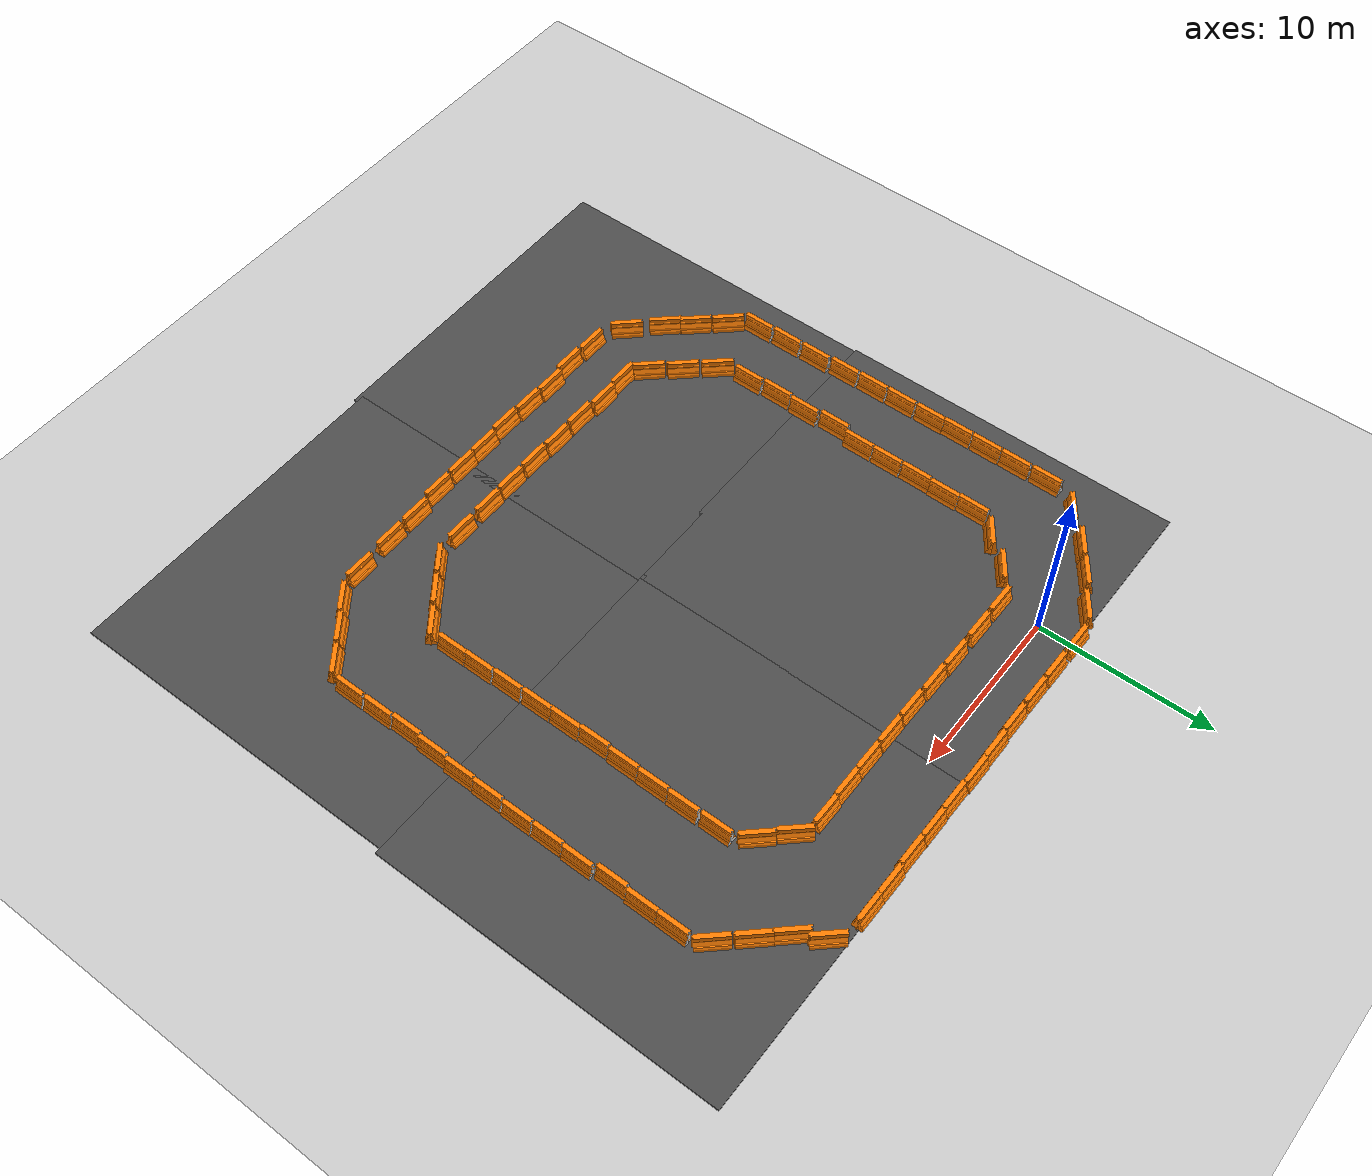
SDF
<sdf version="1.6">
 <world name="default">
  <light name="sun" type="directional">
   <pose>0 0 10 0 -0 0</pose>
   <diffuse>0.8 0.8 0.8 1</diffuse>
   <specular>0.1 0.1 0.1 1</specular>
   <attenuation>
    <range>1000</range>
    <constant>0.9</constant>
    <linear>0.01</linear>
    <quadratic>0.001</quadratic>
   </attenuation>
   <direction>-0.5 0.5 -1</direction>
  </light>
  <model name="ground_plane">
   <static>1</static>
   <link name="link">
    <collision name="collision">
     <geometry><plane><normal>0 0 1</normal><size>100 100</size></plane></geometry>
     <surface><friction><ode><mu>100</mu><mu2>50</mu2></ode></friction></surface>
    </collision>
    <visual name="visual">
     <cast_shadows>0</cast_shadows>
     <geometry><plane><normal>0 0 1</normal><size>100 100</size></plane></geometry>
     <material>
      <script><uri>file://media/materials/scripts/gazebo.material</uri><name>Gazebo/Grey</name></script>
     </material>
    </visual>
   </link>
  </model>
  <gravity>0 0 -9.8</gravity>
  <magnetic_field>6e-06 2.3e-05 -4.2e-05</magnetic_field>
  <atmosphere type="adiabatic"/>
  <physics name="default_physics" default="0" type="ode">
   <max_step_size>0.001</max_step_size>
   <real_time_factor>1</real_time_factor>
   <real_time_update_rate>1000</real_time_update_rate>
  </physics>
  <scene><ambient>0.4 0.4 0.4 1</ambient><background>0.7 0.7 0.7 1</background><shadows>1</shadows></scene>
  <spherical_coordinates>
   <surface_model>EARTH_WGS84</surface_model>
   <latitude_deg>0</latitude_deg>
   <longitude_deg>0</longitude_deg>
   <elevation>0</elevation>
   <heading_deg>0</heading_deg>
  </spherical_coordinates>
  <model name="drc_practice_organge_jersey_barrier_clone">
   <static>1</static>
   <link name="link">
    <visual name="visual">
     <geometry>
      <mesh>
       <uri>model://drc_practice_orange_jersey_barrier/meshes/jersey_barrier.dae</uri>
       <scale>1 1 1</scale>
      </mesh>
     </geometry>
    </visual>
    <collision name="collision">
     <geometry>
      <mesh>
       <uri>model://drc_practice_orange_jersey_barrier/meshes/jersey_barrier.dae</uri>
       <scale>1 1 1</scale>
      </mesh>
     </geometry>
    </collision>
   </link>
   <pose>2.03392 2.10373 0 0 -0 1.57</pose>
  </model>
  <model name="drc_practice_organge_jersey_barrier_clone_0">
   <static>1</static>
   <link name="link">
    <visual name="visual">
     <geometry>
      <mesh>
       <uri>model://drc_practice_orange_jersey_barrier/meshes/jersey_barrier.dae</uri>
       <scale>1 1 1</scale>
      </mesh>
     </geometry>
    </visual>
    <collision name="collision">
     <geometry>
      <mesh>
       <uri>model://drc_practice_orange_jersey_barrier/meshes/jersey_barrier.dae</uri>
       <scale>1 1 1</scale>
      </mesh>
     </geometry>
    </collision>
   </link>
   <pose>3.91145 2.07901 0 0 -0 1.57</pose>
  </model>
  <model name="drc_practice_organge_jersey_barrier_clone_1">
   <static>1</static>
   <link name="link">
    <visual name="visual">
     <geometry>
      <mesh>
       <uri>model://drc_practice_orange_jersey_barrier/meshes/jersey_barrier.dae</uri>
       <scale>1 1 1</scale>
      </mesh>
     </geometry>
    </visual>
    <collision name="collision">
     <geometry>
      <mesh>
       <uri>model://drc_practice_orange_jersey_barrier/meshes/jersey_barrier.dae</uri>
       <scale>1 1 1</scale>
      </mesh>
     </geometry>
    </collision>
   </link>
   <pose>5.86428 2.08634 0 0 -0 1.57</pose>
  </model>
  <model name="drc_practice_organge_jersey_barrier_clone_2">
   <static>1</static>
   <link name="link">
    <visual name="visual">
     <geometry>
      <mesh>
       <uri>model://drc_practice_orange_jersey_barrier/meshes/jersey_barrier.dae</uri>
       <scale>1 1 1</scale>
      </mesh>
     </geometry>
    </visual>
    <collision name="collision">
     <geometry>
      <mesh>
       <uri>model://drc_practice_orange_jersey_barrier/meshes/jersey_barrier.dae</uri>
       <scale>1 1 1</scale>
      </mesh>
     </geometry>
    </collision>
   </link>
   <pose>7.6963 2.14853 0 0 -0 1.57</pose>
  </model>
  <model name="drc_practice_organge_jersey_barrier_clone_3">
   <static>1</static>
   <link name="link">
    <visual name="visual">
     <geometry>
      <mesh>
       <uri>model://drc_practice_orange_jersey_barrier/meshes/jersey_barrier.dae</uri>
       <scale>1 1 1</scale>
      </mesh>
     </geometry>
    </visual>
    <collision name="collision">
     <geometry>
      <mesh>
       <uri>model://drc_practice_orange_jersey_barrier/meshes/jersey_barrier.dae</uri>
       <scale>1 1 1</scale>
      </mesh>
     </geometry>
    </collision>
   </link>
   <pose>9.47957 2.17157 0 0 -0 1.57</pose>
  </model>
  <model name="drc_practice_organge_jersey_barrier_clone_4">
   <static>1</static>
   <link name="link">
    <visual name="visual">
     <geometry>
      <mesh>
       <uri>model://drc_practice_orange_jersey_barrier/meshes/jersey_barrier.dae</uri>
       <scale>1 1 1</scale>
      </mesh>
     </geometry>
    </visual>
    <collision name="collision">
     <geometry>
      <mesh>
       <uri>model://drc_practice_orange_jersey_barrier/meshes/jersey_barrier.dae</uri>
       <scale>1 1 1</scale>
      </mesh>
     </geometry>
    </collision>
   </link>
   <pose>11.2947 2.1082 0 0 -0 1.57</pose>
  </model>
  <model name="drc_practice_organge_jersey_barrier_clone_5">
   <static>1</static>
   <link name="link">
    <visual name="visual">
     <geometry>
      <mesh>
       <uri>model://drc_practice_orange_jersey_barrier/meshes/jersey_barrier.dae</uri>
       <scale>1 1 1</scale>
      </mesh>
     </geometry>
    </visual>
    <collision name="collision">
     <geometry>
      <mesh>
       <uri>model://drc_practice_orange_jersey_barrier/meshes/jersey_barrier.dae</uri>
       <scale>1 1 1</scale>
      </mesh>
     </geometry>
    </collision>
   </link>
   <pose>13.1056 2.12639 0 0 -0 1.57</pose>
  </model>
  <model name="drc_practice_organge_jersey_barrier_clone_6">
   <static>1</static>
   <link name="link">
    <visual name="visual">
     <geometry>
      <mesh>
       <uri>model://drc_practice_orange_jersey_barrier/meshes/jersey_barrier.dae</uri>
       <scale>1 1 1</scale>
      </mesh>
     </geometry>
    </visual>
    <collision name="collision">
     <geometry>
      <mesh>
       <uri>model://drc_practice_orange_jersey_barrier/meshes/jersey_barrier.dae</uri>
       <scale>1 1 1</scale>
      </mesh>
     </geometry>
    </collision>
   </link>
   <pose>14.9117 2.103 0 0 -0 1.57</pose>
  </model>
  <model name="drc_practice_organge_jersey_barrier_clone_7">
   <static>1</static>
   <link name="link">
    <visual name="visual">
     <geometry>
      <mesh>
       <uri>model://drc_practice_orange_jersey_barrier/meshes/jersey_barrier.dae</uri>
       <scale>1 1 1</scale>
      </mesh>
     </geometry>
    </visual>
    <collision name="collision">
     <geometry>
      <mesh>
       <uri>model://drc_practice_orange_jersey_barrier/meshes/jersey_barrier.dae</uri>
       <scale>1 1 1</scale>
      </mesh>
     </geometry>
    </collision>
   </link>
   <pose>0.29978 -2.17018 0 0 -0 1.57</pose>
  </model>
  <model name="drc_practice_organge_jersey_barrier_clone_8">
   <static>1</static>
   <link name="link">
    <visual name="visual">
     <geometry>
      <mesh>
       <uri>model://drc_practice_orange_jersey_barrier/meshes/jersey_barrier.dae</uri>
       <scale>1 1 1</scale>
      </mesh>
     </geometry>
    </visual>
    <collision name="collision">
     <geometry>
      <mesh>
       <uri>model://drc_practice_orange_jersey_barrier/meshes/jersey_barrier.dae</uri>
       <scale>1 1 1</scale>
      </mesh>
     </geometry>
    </collision>
   </link>
   <pose>2.31191 -2.17393 0 0 -0 1.57</pose>
  </model>
  <model name="drc_practice_organge_jersey_barrier_clone_9">
   <static>1</static>
   <link name="link">
    <visual name="visual">
     <geometry>
      <mesh>
       <uri>model://drc_practice_orange_jersey_barrier/meshes/jersey_barrier.dae</uri>
       <scale>1 1 1</scale>
      </mesh>
     </geometry>
    </visual>
    <collision name="collision">
     <geometry>
      <mesh>
       <uri>model://drc_practice_orange_jersey_barrier/meshes/jersey_barrier.dae</uri>
       <scale>1 1 1</scale>
      </mesh>
     </geometry>
    </collision>
   </link>
   <pose>4.47094 -2.1777 0 0 -0 1.57</pose>
  </model>
  <model name="drc_practice_organge_jersey_barrier_clone_10">
   <static>1</static>
   <link name="link">
    <visual name="visual">
     <geometry>
      <mesh>
       <uri>model://drc_practice_orange_jersey_barrier/meshes/jersey_barrier.dae</uri>
       <scale>1 1 1</scale>
      </mesh>
     </geometry>
    </visual>
    <collision name="collision">
     <geometry>
      <mesh>
       <uri>model://drc_practice_orange_jersey_barrier/meshes/jersey_barrier.dae</uri>
       <scale>1 1 1</scale>
      </mesh>
     </geometry>
    </collision>
   </link>
   <pose>6.33529 -2.22935 0 0 -0 1.57</pose>
  </model>
  <model name="drc_practice_organge_jersey_barrier_clone_11">
   <static>1</static>
   <link name="link">
    <visual name="visual">
     <geometry>
      <mesh>
       <uri>model://drc_practice_orange_jersey_barrier/meshes/jersey_barrier.dae</uri>
       <scale>1 1 1</scale>
      </mesh>
     </geometry>
    </visual>
    <collision name="collision">
     <geometry>
      <mesh>
       <uri>model://drc_practice_orange_jersey_barrier/meshes/jersey_barrier.dae</uri>
       <scale>1 1 1</scale>
      </mesh>
     </geometry>
    </collision>
   </link>
   <pose>8.25952 -2.28963 0 0 -0 1.57</pose>
  </model>
  <model name="drc_practice_organge_jersey_barrier_clone_12">
   <static>1</static>
   <link name="link">
    <visual name="visual">
     <geometry>
      <mesh>
       <uri>model://drc_practice_orange_jersey_barrier/meshes/jersey_barrier.dae</uri>
       <scale>1 1 1</scale>
      </mesh>
     </geometry>
    </visual>
    <collision name="collision">
     <geometry>
      <mesh>
       <uri>model://drc_practice_orange_jersey_barrier/meshes/jersey_barrier.dae</uri>
       <scale>1 1 1</scale>
      </mesh>
     </geometry>
    </collision>
   </link>
   <pose>10.1379 -2.29515 0 0 -0 1.57</pose>
  </model>
  <model name="drc_practice_organge_jersey_barrier_clone_13">
   <static>1</static>
   <link name="link">
    <visual name="visual">
     <geometry>
      <mesh>
       <uri>model://drc_practice_orange_jersey_barrier/meshes/jersey_barrier.dae</uri>
       <scale>1 1 1</scale>
      </mesh>
     </geometry>
    </visual>
    <collision name="collision">
     <geometry>
      <mesh>
       <uri>model://drc_practice_orange_jersey_barrier/meshes/jersey_barrier.dae</uri>
       <scale>1 1 1</scale>
      </mesh>
     </geometry>
    </collision>
   </link>
   <pose>12.0033 -2.29598 0 0 -0 1.57</pose>
  </model>
  <model name="drc_practice_organge_jersey_barrier_clone_14">
   <static>1</static>
   <link name="link">
    <visual name="visual">
     <geometry>
      <mesh>
       <uri>model://drc_practice_orange_jersey_barrier/meshes/jersey_barrier.dae</uri>
       <scale>1 1 1</scale>
      </mesh>
     </geometry>
    </visual>
    <collision name="collision">
     <geometry>
      <mesh>
       <uri>model://drc_practice_orange_jersey_barrier/meshes/jersey_barrier.dae</uri>
       <scale>1 1 1</scale>
      </mesh>
     </geometry>
    </collision>
   </link>
   <pose>13.8028 -2.28455 0 0 -0 1.57</pose>
  </model>
  <model name="drc_practice_organge_jersey_barrier_clone_15">
   <static>1</static>
   <link name="link">
    <visual name="visual">
     <geometry>
      <mesh>
       <uri>model://drc_practice_orange_jersey_barrier/meshes/jersey_barrier.dae</uri>
       <scale>1 1 1</scale>
      </mesh>
     </geometry>
    </visual>
    <collision name="collision">
     <geometry>
      <mesh>
       <uri>model://drc_practice_orange_jersey_barrier/meshes/jersey_barrier.dae</uri>
       <scale>1 1 1</scale>
      </mesh>
     </geometry>
    </collision>
   </link>
   <pose>15.5891 -2.23625 0 0 -0 1.57</pose>
  </model>
  <model name="drc_practice_organge_jersey_barrier_clone_16">
   <static>1</static>
   <link name="link">
    <visual name="visual">
     <geometry>
      <mesh>
       <uri>model://drc_practice_orange_jersey_barrier/meshes/jersey_barrier.dae</uri>
       <scale>1 1 1</scale>
      </mesh>
     </geometry>
    </visual>
    <collision name="collision">
     <geometry>
      <mesh>
       <uri>model://drc_practice_orange_jersey_barrier/meshes/jersey_barrier.dae</uri>
       <scale>1 1 1</scale>
      </mesh>
     </geometry>
    </collision>
   </link>
   <pose>16.7665 2.17186 0 0 -0 1.57</pose>
  </model>
  <model name="drc_practice_organge_jersey_barrier_clone_17">
   <static>1</static>
   <link name="link">
    <visual name="visual">
     <geometry>
      <mesh>
       <uri>model://drc_practice_orange_jersey_barrier/meshes/jersey_barrier.dae</uri>
       <scale>1 1 1</scale>
      </mesh>
     </geometry>
    </visual>
    <collision name="collision">
     <geometry>
      <mesh>
       <uri>model://drc_practice_orange_jersey_barrier/meshes/jersey_barrier.dae</uri>
       <scale>1 1 1</scale>
      </mesh>
     </geometry>
    </collision>
   </link>
   <pose>18.5078 2.16757 0 0 -0 1.57</pose>
  </model>
  <model name="drc_practice_organge_jersey_barrier_clone_18_clone">
   <static>1</static>
   <link name="link">
    <visual name="visual">
     <geometry>
      <mesh>
       <uri>model://drc_practice_orange_jersey_barrier/meshes/jersey_barrier.dae</uri>
       <scale>1 1 1</scale>
      </mesh>
     </geometry>
    </visual>
    <collision name="collision">
     <geometry>
      <mesh>
       <uri>model://drc_practice_orange_jersey_barrier/meshes/jersey_barrier.dae</uri>
       <scale>1 1 1</scale>
      </mesh>
     </geometry>
    </collision>
   </link>
   <pose>17.3121 -2.74363 0 0 -0 0.75</pose>
  </model>
  <model name="drc_practice_organge_jersey_barrier_clone_18_clone_0">
   <static>1</static>
   <link name="link">
    <visual name="visual">
     <geometry>
      <mesh>
       <uri>model://drc_practice_orange_jersey_barrier/meshes/jersey_barrier.dae</uri>
       <scale>1 1 1</scale>
      </mesh>
     </geometry>
    </visual>
    <collision name="collision">
     <geometry>
      <mesh>
       <uri>model://drc_practice_orange_jersey_barrier/meshes/jersey_barrier.dae</uri>
       <scale>1 1 1</scale>
      </mesh>
     </geometry>
    </collision>
   </link>
   <pose>18.6026 -4.02925 0 0 -0 0.75</pose>
  </model>
  <model name="drc_practice_organge_jersey_barrier_clone_18_clone_1">
   <static>1</static>
   <link name="link">
    <visual name="visual">
     <geometry>
      <mesh>
       <uri>model://drc_practice_orange_jersey_barrier/meshes/jersey_barrier.dae</uri>
       <scale>1 1 1</scale>
      </mesh>
     </geometry>
    </visual>
    <collision name="collision">
     <geometry>
      <mesh>
       <uri>model://drc_practice_orange_jersey_barrier/meshes/jersey_barrier.dae</uri>
       <scale>1 1 1</scale>
      </mesh>
     </geometry>
    </collision>
   </link>
   <pose>21.567 0.12109 0 0 -0 0.75</pose>
  </model>
  <model name="drc_practice_organge_jersey_barrier_clone_18_clone_2">
   <static>1</static>
   <link name="link">
    <visual name="visual">
     <geometry>
      <mesh>
       <uri>model://drc_practice_orange_jersey_barrier/meshes/jersey_barrier.dae</uri>
       <scale>1 1 1</scale>
      </mesh>
     </geometry>
    </visual>
    <collision name="collision">
     <geometry>
      <mesh>
       <uri>model://drc_practice_orange_jersey_barrier/meshes/jersey_barrier.dae</uri>
       <scale>1 1 1</scale>
      </mesh>
     </geometry>
    </collision>
   </link>
   <pose>22.7772 -1.16386 0 0 -0 0.75</pose>
  </model>
  <model name="drc_practice_organge_jersey_barrier_clone_18_clone_3">
   <static>1</static>
   <link name="link">
    <visual name="visual">
     <geometry>
      <mesh>
       <uri>model://drc_practice_orange_jersey_barrier/meshes/jersey_barrier.dae</uri>
       <scale>1 1 1</scale>
      </mesh>
     </geometry>
    </visual>
    <collision name="collision">
     <geometry>
      <mesh>
       <uri>model://drc_practice_orange_jersey_barrier/meshes/jersey_barrier.dae</uri>
       <scale>1 1 1</scale>
      </mesh>
     </geometry>
    </collision>
   </link>
   <pose>24.0499 -2.547 0 0 -0 0.75</pose>
  </model>
  <model name="drc_practice_organge_jersey_barrier_0">
   <static>1</static>
   <link name="link">
    <visual name="visual">
     <geometry>
      <mesh>
       <uri>model://drc_practice_orange_jersey_barrier/meshes/jersey_barrier.dae</uri>
       <scale>1 1 1</scale>
      </mesh>
     </geometry>
    </visual>
    <collision name="collision">
     <geometry>
      <mesh>
       <uri>model://drc_practice_orange_jersey_barrier/meshes/jersey_barrier.dae</uri>
       <scale>1 1 1</scale>
      </mesh>
     </geometry>
    </collision>
   </link>
   <pose>19.3502 -5.80301 0 0 -0 0</pose>
  </model>
  <model name="drc_practice_organge_jersey_barrier_0_clone">
   <static>1</static>
   <link name="link">
    <visual name="visual">
     <geometry>
      <mesh>
       <uri>model://drc_practice_orange_jersey_barrier/meshes/jersey_barrier.dae</uri>
       <scale>1 1 1</scale>
      </mesh>
     </geometry>
    </visual>
    <collision name="collision">
     <geometry>
      <mesh>
       <uri>model://drc_practice_orange_jersey_barrier/meshes/jersey_barrier.dae</uri>
       <scale>1 1 1</scale>
      </mesh>
     </geometry>
    </collision>
   </link>
   <pose>24.5941 -4.31776 0 0 -0 0</pose>
  </model>
  <model name="drc_practice_organge_jersey_barrier_0_clone_0">
   <static>1</static>
   <link name="link">
    <visual name="visual">
     <geometry>
      <mesh>
       <uri>model://drc_practice_orange_jersey_barrier/meshes/jersey_barrier.dae</uri>
       <scale>1 1 1</scale>
      </mesh>
     </geometry>
    </visual>
    <collision name="collision">
     <geometry>
      <mesh>
       <uri>model://drc_practice_orange_jersey_barrier/meshes/jersey_barrier.dae</uri>
       <scale>1 1 1</scale>
      </mesh>
     </geometry>
    </collision>
   </link>
   <pose>19.3686 -7.72709 0 0 -0 0</pose>
  </model>
  <model name="drc_practice_organge_jersey_barrier_0_clone_1">
   <static>1</static>
   <link name="link">
    <visual name="visual">
     <geometry>
      <mesh>
       <uri>model://drc_practice_orange_jersey_barrier/meshes/jersey_barrier.dae</uri>
       <scale>1 1 1</scale>
      </mesh>
     </geometry>
    </visual>
    <collision name="collision">
     <geometry>
      <mesh>
       <uri>model://drc_practice_orange_jersey_barrier/meshes/jersey_barrier.dae</uri>
       <scale>1 1 1</scale>
      </mesh>
     </geometry>
    </collision>
   </link>
   <pose>19.3301 -9.56124 0 0 -0 0</pose>
  </model>
  <model name="drc_practice_organge_jersey_barrier_0_clone_2">
   <static>1</static>
   <link name="link">
    <visual name="visual">
     <geometry>
      <mesh>
       <uri>model://drc_practice_orange_jersey_barrier/meshes/jersey_barrier.dae</uri>
       <scale>1 1 1</scale>
      </mesh>
     </geometry>
    </visual>
    <collision name="collision">
     <geometry>
      <mesh>
       <uri>model://drc_practice_orange_jersey_barrier/meshes/jersey_barrier.dae</uri>
       <scale>1 1 1</scale>
      </mesh>
     </geometry>
    </collision>
   </link>
   <pose>19.2878 -11.3888 0 0 -0 0</pose>
  </model>
  <model name="drc_practice_organge_jersey_barrier_0_clone_3">
   <static>1</static>
   <link name="link">
    <visual name="visual">
     <geometry>
      <mesh>
       <uri>model://drc_practice_orange_jersey_barrier/meshes/jersey_barrier.dae</uri>
       <scale>1 1 1</scale>
      </mesh>
     </geometry>
    </visual>
    <collision name="collision">
     <geometry>
      <mesh>
       <uri>model://drc_practice_orange_jersey_barrier/meshes/jersey_barrier.dae</uri>
       <scale>1 1 1</scale>
      </mesh>
     </geometry>
    </collision>
   </link>
   <pose>19.2012 -13.2458 0 0 -0 0</pose>
  </model>
  <model name="drc_practice_organge_jersey_barrier_0_clone_4">
   <static>1</static>
   <link name="link">
    <visual name="visual">
     <geometry>
      <mesh>
       <uri>model://drc_practice_orange_jersey_barrier/meshes/jersey_barrier.dae</uri>
       <scale>1 1 1</scale>
      </mesh>
     </geometry>
    </visual>
    <collision name="collision">
     <geometry>
      <mesh>
       <uri>model://drc_practice_orange_jersey_barrier/meshes/jersey_barrier.dae</uri>
       <scale>1 1 1</scale>
      </mesh>
     </geometry>
    </collision>
   </link>
   <pose>19.2645 -14.9926 0 0 -0 0</pose>
  </model>
  <model name="drc_practice_organge_jersey_barrier_0_clone_5">
   <static>1</static>
   <link name="link">
    <visual name="visual">
     <geometry>
      <mesh>
       <uri>model://drc_practice_orange_jersey_barrier/meshes/jersey_barrier.dae</uri>
       <scale>1 1 1</scale>
      </mesh>
     </geometry>
    </visual>
    <collision name="collision">
     <geometry>
      <mesh>
       <uri>model://drc_practice_orange_jersey_barrier/meshes/jersey_barrier.dae</uri>
       <scale>1 1 1</scale>
      </mesh>
     </geometry>
    </collision>
   </link>
   <pose>19.2756 -16.7716 0 0 -0 0</pose>
  </model>
  <model name="drc_practice_organge_jersey_barrier_0_clone_6">
   <static>1</static>
   <link name="link">
    <visual name="visual">
     <geometry>
      <mesh>
       <uri>model://drc_practice_orange_jersey_barrier/meshes/jersey_barrier.dae</uri>
       <scale>1 1 1</scale>
      </mesh>
     </geometry>
    </visual>
    <collision name="collision">
     <geometry>
      <mesh>
       <uri>model://drc_practice_orange_jersey_barrier/meshes/jersey_barrier.dae</uri>
       <scale>1 1 1</scale>
      </mesh>
     </geometry>
    </collision>
   </link>
   <pose>24.5831 -6.10753 0 0 -0 0</pose>
  </model>
  <model name="drc_practice_organge_jersey_barrier_0_clone_7">
   <static>1</static>
   <link name="link">
    <visual name="visual">
     <geometry>
      <mesh>
       <uri>model://drc_practice_orange_jersey_barrier/meshes/jersey_barrier.dae</uri>
       <scale>1 1 1</scale>
      </mesh>
     </geometry>
    </visual>
    <collision name="collision">
     <geometry>
      <mesh>
       <uri>model://drc_practice_orange_jersey_barrier/meshes/jersey_barrier.dae</uri>
       <scale>1 1 1</scale>
      </mesh>
     </geometry>
    </collision>
   </link>
   <pose>24.4664 -7.93871 0 0 -0 0</pose>
  </model>
  <model name="drc_practice_organge_jersey_barrier_0_clone_8">
   <static>1</static>
   <link name="link">
    <visual name="visual">
     <geometry>
      <mesh>
       <uri>model://drc_practice_orange_jersey_barrier/meshes/jersey_barrier.dae</uri>
       <scale>1 1 1</scale>
      </mesh>
     </geometry>
    </visual>
    <collision name="collision">
     <geometry>
      <mesh>
       <uri>model://drc_practice_orange_jersey_barrier/meshes/jersey_barrier.dae</uri>
       <scale>1 1 1</scale>
      </mesh>
     </geometry>
    </collision>
   </link>
   <pose>24.6561 -9.83467 0 0 -0 0</pose>
  </model>
  <model name="drc_practice_organge_jersey_barrier_0_clone_9">
   <static>1</static>
   <link name="link">
    <visual name="visual">
     <geometry>
      <mesh>
       <uri>model://drc_practice_orange_jersey_barrier/meshes/jersey_barrier.dae</uri>
       <scale>1 1 1</scale>
      </mesh>
     </geometry>
    </visual>
    <collision name="collision">
     <geometry>
      <mesh>
       <uri>model://drc_practice_orange_jersey_barrier/meshes/jersey_barrier.dae</uri>
       <scale>1 1 1</scale>
      </mesh>
     </geometry>
    </collision>
   </link>
   <pose>24.5999 -11.6545 0 0 -0 0</pose>
  </model>
  <model name="drc_practice_organge_jersey_barrier_0_clone_10">
   <static>1</static>
   <link name="link">
    <visual name="visual">
     <geometry>
      <mesh>
       <uri>model://drc_practice_orange_jersey_barrier/meshes/jersey_barrier.dae</uri>
       <scale>1 1 1</scale>
      </mesh>
     </geometry>
    </visual>
    <collision name="collision">
     <geometry>
      <mesh>
       <uri>model://drc_practice_orange_jersey_barrier/meshes/jersey_barrier.dae</uri>
       <scale>1 1 1</scale>
      </mesh>
     </geometry>
    </collision>
   </link>
   <pose>24.6074 -13.5105 0 0 -0 0</pose>
  </model>
  <model name="drc_practice_organge_jersey_barrier_0_clone_11">
   <static>1</static>
   <link name="link">
    <visual name="visual">
     <geometry>
      <mesh>
       <uri>model://drc_practice_orange_jersey_barrier/meshes/jersey_barrier.dae</uri>
       <scale>1 1 1</scale>
      </mesh>
     </geometry>
    </visual>
    <collision name="collision">
     <geometry>
      <mesh>
       <uri>model://drc_practice_orange_jersey_barrier/meshes/jersey_barrier.dae</uri>
       <scale>1 1 1</scale>
      </mesh>
     </geometry>
    </collision>
   </link>
   <pose>24.5473 -15.3984 0 0 -0 0</pose>
  </model>
  <model name="drc_practice_organge_jersey_barrier_0_clone_12">
   <static>1</static>
   <link name="link">
    <visual name="visual">
     <geometry>
      <mesh>
       <uri>model://drc_practice_orange_jersey_barrier/meshes/jersey_barrier.dae</uri>
       <scale>1 1 1</scale>
      </mesh>
     </geometry>
    </visual>
    <collision name="collision">
     <geometry>
      <mesh>
       <uri>model://drc_practice_orange_jersey_barrier/meshes/jersey_barrier.dae</uri>
       <scale>1 1 1</scale>
      </mesh>
     </geometry>
    </collision>
   </link>
   <pose>24.4937 -17.2004 0 0 -0 0</pose>
  </model>
  <model name="drc_practice_organge_jersey_barrier_0_clone_13">
   <static>1</static>
   <link name="link">
    <visual name="visual">
     <geometry>
      <mesh>
       <uri>model://drc_practice_orange_jersey_barrier/meshes/jersey_barrier.dae</uri>
       <scale>1 1 1</scale>
      </mesh>
     </geometry>
    </visual>
    <collision name="collision">
     <geometry>
      <mesh>
       <uri>model://drc_practice_orange_jersey_barrier/meshes/jersey_barrier.dae</uri>
       <scale>1 1 1</scale>
      </mesh>
     </geometry>
    </collision>
   </link>
   <pose>24.3746 -19.0288 0 0 -0 0</pose>
  </model>
  <model name="drc_practice_organge_jersey_barrier_0_clone_14">
   <static>1</static>
   <link name="link">
    <visual name="visual">
     <geometry>
      <mesh>
       <uri>model://drc_practice_orange_jersey_barrier/meshes/jersey_barrier.dae</uri>
       <scale>1 1 1</scale>
      </mesh>
     </geometry>
    </visual>
    <collision name="collision">
     <geometry>
      <mesh>
       <uri>model://drc_practice_orange_jersey_barrier/meshes/jersey_barrier.dae</uri>
       <scale>1 1 1</scale>
      </mesh>
     </geometry>
    </collision>
   </link>
   <pose>24.2561 -20.8065 0 0 -0 0</pose>
  </model>
  <model name="drc_practice_organge_jersey_barrier_0_clone_15">
   <static>1</static>
   <link name="link">
    <visual name="visual">
     <geometry>
      <mesh>
       <uri>model://drc_practice_orange_jersey_barrier/meshes/jersey_barrier.dae</uri>
       <scale>1 1 1</scale>
      </mesh>
     </geometry>
    </visual>
    <collision name="collision">
     <geometry>
      <mesh>
       <uri>model://drc_practice_orange_jersey_barrier/meshes/jersey_barrier.dae</uri>
       <scale>1 1 1</scale>
      </mesh>
     </geometry>
    </collision>
   </link>
   <pose>24.3223 -22.6057 0 0 -0 0</pose>
  </model>
  <model name="drc_practice_organge_jersey_barrier_0_clone_16">
   <static>1</static>
   <link name="link">
    <visual name="visual">
     <geometry>
      <mesh>
       <uri>model://drc_practice_orange_jersey_barrier/meshes/jersey_barrier.dae</uri>
       <scale>1 1 1</scale>
      </mesh>
     </geometry>
    </visual>
    <collision name="collision">
     <geometry>
      <mesh>
       <uri>model://drc_practice_orange_jersey_barrier/meshes/jersey_barrier.dae</uri>
       <scale>1 1 1</scale>
      </mesh>
     </geometry>
    </collision>
   </link>
   <pose>24.3288 -24.4741 0 0 -0 0</pose>
  </model>
  <model name="drc_practice_organge_jersey_barrier_0_clone_17">
   <static>1</static>
   <link name="link">
    <visual name="visual">
     <geometry>
      <mesh>
       <uri>model://drc_practice_orange_jersey_barrier/meshes/jersey_barrier.dae</uri>
       <scale>1 1 1</scale>
      </mesh>
     </geometry>
    </visual>
    <collision name="collision">
     <geometry>
      <mesh>
       <uri>model://drc_practice_orange_jersey_barrier/meshes/jersey_barrier.dae</uri>
       <scale>1 1 1</scale>
      </mesh>
     </geometry>
    </collision>
   </link>
   <pose>19.3052 -18.6351 0 0 -0 0</pose>
  </model>
  <model name="drc_practice_organge_jersey_barrier_0_clone_18">
   <static>1</static>
   <link name="link">
    <visual name="visual">
     <geometry>
      <mesh>
       <uri>model://drc_practice_orange_jersey_barrier/meshes/jersey_barrier.dae</uri>
       <scale>1 1 1</scale>
      </mesh>
     </geometry>
    </visual>
    <collision name="collision">
     <geometry>
      <mesh>
       <uri>model://drc_practice_orange_jersey_barrier/meshes/jersey_barrier.dae</uri>
       <scale>1 1 1</scale>
      </mesh>
     </geometry>
    </collision>
   </link>
   <pose>19.3585 -20.4421 0 0 -0 0</pose>
  </model>
  <model name="drc_practice_organge_jersey_barrier_0_clone_19">
   <static>1</static>
   <link name="link">
    <visual name="visual">
     <geometry>
      <mesh>
       <uri>model://drc_practice_orange_jersey_barrier/meshes/jersey_barrier.dae</uri>
       <scale>1 1 1</scale>
      </mesh>
     </geometry>
    </visual>
    <collision name="collision">
     <geometry>
      <mesh>
       <uri>model://drc_practice_orange_jersey_barrier/meshes/jersey_barrier.dae</uri>
       <scale>1 1 1</scale>
      </mesh>
     </geometry>
    </collision>
   </link>
   <pose>19.3721 -22.1895 0 0 -0 0</pose>
  </model>
  <model name="drc_practice_organge_jersey_barrier_clone_18_clone_clone_clone">
   <static>1</static>
   <link name="link">
    <visual name="visual">
     <geometry>
      <mesh>
       <uri>model://drc_practice_orange_jersey_barrier/meshes/jersey_barrier.dae</uri>
       <scale>1 1 1</scale>
      </mesh>
     </geometry>
    </visual>
    <collision name="collision">
     <geometry>
      <mesh>
       <uri>model://drc_practice_orange_jersey_barrier/meshes/jersey_barrier.dae</uri>
       <scale>1 1 1</scale>
      </mesh>
     </geometry>
    </collision>
   </link>
   <pose>23.6163 -26.263 0 0 -0 2.2</pose>
  </model>
  <model name="drc_practice_organge_jersey_barrier_clone_18_clone_clone_clone_0">
   <static>1</static>
   <link name="link">
    <visual name="visual">
     <geometry>
      <mesh>
       <uri>model://drc_practice_orange_jersey_barrier/meshes/jersey_barrier.dae</uri>
       <scale>1 1 1</scale>
      </mesh>
     </geometry>
    </visual>
    <collision name="collision">
     <geometry>
      <mesh>
       <uri>model://drc_practice_orange_jersey_barrier/meshes/jersey_barrier.dae</uri>
       <scale>1 1 1</scale>
      </mesh>
     </geometry>
    </collision>
   </link>
   <pose>17.3683 -25.1779 0 0 -0 2.2</pose>
  </model>
  <model name="drc_practice_organge_jersey_barrier_clone_18_clone_clone_clone_1">
   <static>1</static>
   <link name="link">
    <visual name="visual">
     <geometry>
      <mesh>
       <uri>model://drc_practice_orange_jersey_barrier/meshes/jersey_barrier.dae</uri>
       <scale>1 1 1</scale>
      </mesh>
     </geometry>
    </visual>
    <collision name="collision">
     <geometry>
      <mesh>
       <uri>model://drc_practice_orange_jersey_barrier/meshes/jersey_barrier.dae</uri>
       <scale>1 1 1</scale>
      </mesh>
     </geometry>
    </collision>
   </link>
   <pose>22.0705 -27.4207 0 0 -0 2.2</pose>
  </model>
  <model name="drc_practice_organge_jersey_barrier_clone_18_clone_clone_clone_2">
   <static>1</static>
   <link name="link">
    <visual name="visual">
     <geometry>
      <mesh>
       <uri>model://drc_practice_orange_jersey_barrier/meshes/jersey_barrier.dae</uri>
       <scale>1 1 1</scale>
      </mesh>
     </geometry>
    </visual>
    <collision name="collision">
     <geometry>
      <mesh>
       <uri>model://drc_practice_orange_jersey_barrier/meshes/jersey_barrier.dae</uri>
       <scale>1 1 1</scale>
      </mesh>
     </geometry>
    </collision>
   </link>
   <pose>15.8063 -26.3115 0 0 -0 2.2</pose>
  </model>
  <model name="drc_practice_organge_jersey_barrier_clone_18_clone_clone_clone_3">
   <static>1</static>
   <link name="link">
    <visual name="visual">
     <geometry>
      <mesh>
       <uri>model://drc_practice_orange_jersey_barrier/meshes/jersey_barrier.dae</uri>
       <scale>1 1 1</scale>
      </mesh>
     </geometry>
    </visual>
    <collision name="collision">
     <geometry>
      <mesh>
       <uri>model://drc_practice_orange_jersey_barrier/meshes/jersey_barrier.dae</uri>
       <scale>1 1 1</scale>
      </mesh>
     </geometry>
    </collision>
   </link>
   <pose>20.6147 -28.5779 0 0 -0 2.2</pose>
  </model>
  <model name="drc_practice_organge_jersey_barrier_clone_11_clone">
   <static>1</static>
   <link name="link">
    <visual name="visual">
     <geometry>
      <mesh>
       <uri>model://drc_practice_orange_jersey_barrier/meshes/jersey_barrier.dae</uri>
       <scale>1 1 1</scale>
      </mesh>
     </geometry>
    </visual>
    <collision name="collision">
     <geometry>
      <mesh>
       <uri>model://drc_practice_orange_jersey_barrier/meshes/jersey_barrier.dae</uri>
       <scale>1 1 1</scale>
      </mesh>
     </geometry>
    </collision>
   </link>
   <pose>13.582 -26.7517 0 0 -0 1.57</pose>
  </model>
  <model name="drc_practice_organge_jersey_barrier_clone_11_clone_0">
   <static>1</static>
   <link name="link">
    <visual name="visual">
     <geometry>
      <mesh>
       <uri>model://drc_practice_orange_jersey_barrier/meshes/jersey_barrier.dae</uri>
       <scale>1 1 1</scale>
      </mesh>
     </geometry>
    </visual>
    <collision name="collision">
     <geometry>
      <mesh>
       <uri>model://drc_practice_orange_jersey_barrier/meshes/jersey_barrier.dae</uri>
       <scale>1 1 1</scale>
      </mesh>
     </geometry>
    </collision>
   </link>
   <pose>18.6544 -29.2073 0 0 -0 1.57</pose>
  </model>
  <model name="drc_practice_organge_jersey_barrier_clone_11_clone_1">
   <static>1</static>
   <link name="link">
    <visual name="visual">
     <geometry>
      <mesh>
       <uri>model://drc_practice_orange_jersey_barrier/meshes/jersey_barrier.dae</uri>
       <scale>1 1 1</scale>
      </mesh>
     </geometry>
    </visual>
    <collision name="collision">
     <geometry>
      <mesh>
       <uri>model://drc_practice_orange_jersey_barrier/meshes/jersey_barrier.dae</uri>
       <scale>1 1 1</scale>
      </mesh>
     </geometry>
    </collision>
   </link>
   <pose>16.2429 -29.3338 0 0 -0 1.57</pose>
  </model>
  <model name="drc_practice_organge_jersey_barrier_clone_11_clone_2">
   <static>1</static>
   <link name="link">
    <visual name="visual">
     <geometry>
      <mesh>
       <uri>model://drc_practice_orange_jersey_barrier/meshes/jersey_barrier.dae</uri>
       <scale>1 1 1</scale>
      </mesh>
     </geometry>
    </visual>
    <collision name="collision">
     <geometry>
      <mesh>
       <uri>model://drc_practice_orange_jersey_barrier/meshes/jersey_barrier.dae</uri>
       <scale>1 1 1</scale>
      </mesh>
     </geometry>
    </collision>
   </link>
   <pose>14.2334 -29.3644 0 0 -0 1.57</pose>
  </model>
  <model name="drc_practice_organge_jersey_barrier_clone_11_clone_3">
   <static>1</static>
   <link name="link">
    <visual name="visual">
     <geometry>
      <mesh>
       <uri>model://drc_practice_orange_jersey_barrier/meshes/jersey_barrier.dae</uri>
       <scale>1 1 1</scale>
      </mesh>
     </geometry>
    </visual>
    <collision name="collision">
     <geometry>
      <mesh>
       <uri>model://drc_practice_orange_jersey_barrier/meshes/jersey_barrier.dae</uri>
       <scale>1 1 1</scale>
      </mesh>
     </geometry>
    </collision>
   </link>
   <pose>11.4436 -26.7753 0 0 -0 1.57</pose>
  </model>
  <model name="drc_practice_organge_jersey_barrier_clone_11_clone_4">
   <static>1</static>
   <link name="link">
    <visual name="visual">
     <geometry>
      <mesh>
       <uri>model://drc_practice_orange_jersey_barrier/meshes/jersey_barrier.dae</uri>
       <scale>1 1 1</scale>
      </mesh>
     </geometry>
    </visual>
    <collision name="collision">
     <geometry>
      <mesh>
       <uri>model://drc_practice_orange_jersey_barrier/meshes/jersey_barrier.dae</uri>
       <scale>1 1 1</scale>
      </mesh>
     </geometry>
    </collision>
   </link>
   <pose>12.2715 -29.5613 0 0 -0 1.57</pose>
  </model>
  <model name="drc_practice_organge_jersey_barrier_clone_11_clone_5">
   <static>1</static>
   <link name="link">
    <visual name="visual">
     <geometry>
      <mesh>
       <uri>model://drc_practice_orange_jersey_barrier/meshes/jersey_barrier.dae</uri>
       <scale>1 1 1</scale>
      </mesh>
     </geometry>
    </visual>
    <collision name="collision">
     <geometry>
      <mesh>
       <uri>model://drc_practice_orange_jersey_barrier/meshes/jersey_barrier.dae</uri>
       <scale>1 1 1</scale>
      </mesh>
     </geometry>
    </collision>
   </link>
   <pose>10.3329 -29.5871 0 0 -0 1.57</pose>
  </model>
  <model name="drc_practice_organge_jersey_barrier_clone_11_clone_6">
   <static>1</static>
   <link name="link">
    <visual name="visual">
     <geometry>
      <mesh>
       <uri>model://drc_practice_orange_jersey_barrier/meshes/jersey_barrier.dae</uri>
       <scale>1 1 1</scale>
      </mesh>
     </geometry>
    </visual>
    <collision name="collision">
     <geometry>
      <mesh>
       <uri>model://drc_practice_orange_jersey_barrier/meshes/jersey_barrier.dae</uri>
       <scale>1 1 1</scale>
      </mesh>
     </geometry>
    </collision>
   </link>
   <pose>8.50157 -29.6065 0 0 -0 1.57</pose>
  </model>
  <model name="drc_practice_organge_jersey_barrier_clone_11_clone_7">
   <static>1</static>
   <link name="link">
    <visual name="visual">
     <geometry>
      <mesh>
       <uri>model://drc_practice_orange_jersey_barrier/meshes/jersey_barrier.dae</uri>
       <scale>1 1 1</scale>
      </mesh>
     </geometry>
    </visual>
    <collision name="collision">
     <geometry>
      <mesh>
       <uri>model://drc_practice_orange_jersey_barrier/meshes/jersey_barrier.dae</uri>
       <scale>1 1 1</scale>
      </mesh>
     </geometry>
    </collision>
   </link>
   <pose>9.55315 -26.8139 0 0 -0 1.57</pose>
  </model>
  <model name="drc_practice_organge_jersey_barrier_clone_11_clone_8">
   <static>1</static>
   <link name="link">
    <visual name="visual">
     <geometry>
      <mesh>
       <uri>model://drc_practice_orange_jersey_barrier/meshes/jersey_barrier.dae</uri>
       <scale>1 1 1</scale>
      </mesh>
     </geometry>
    </visual>
    <collision name="collision">
     <geometry>
      <mesh>
       <uri>model://drc_practice_orange_jersey_barrier/meshes/jersey_barrier.dae</uri>
       <scale>1 1 1</scale>
      </mesh>
     </geometry>
    </collision>
   </link>
   <pose>7.62658 -26.8354 0 0 -0 1.57</pose>
  </model>
  <model name="drc_practice_organge_jersey_barrier_clone_11_clone_9">
   <static>1</static>
   <link name="link">
    <visual name="visual">
     <geometry>
      <mesh>
       <uri>model://drc_practice_orange_jersey_barrier/meshes/jersey_barrier.dae</uri>
       <scale>1 1 1</scale>
      </mesh>
     </geometry>
    </visual>
    <collision name="collision">
     <geometry>
      <mesh>
       <uri>model://drc_practice_orange_jersey_barrier/meshes/jersey_barrier.dae</uri>
       <scale>1 1 1</scale>
      </mesh>
     </geometry>
    </collision>
   </link>
   <pose>6.61724 -29.7196 0 0 -0 1.57</pose>
  </model>
  <model name="drc_practice_organge_jersey_barrier_clone_11_clone_10">
   <static>1</static>
   <link name="link">
    <visual name="visual">
     <geometry>
      <mesh>
       <uri>model://drc_practice_orange_jersey_barrier/meshes/jersey_barrier.dae</uri>
       <scale>1 1 1</scale>
      </mesh>
     </geometry>
    </visual>
    <collision name="collision">
     <geometry>
      <mesh>
       <uri>model://drc_practice_orange_jersey_barrier/meshes/jersey_barrier.dae</uri>
       <scale>1 1 1</scale>
      </mesh>
     </geometry>
    </collision>
   </link>
   <pose>4.78558 -29.6426 0 0 -0 1.57</pose>
  </model>
  <model name="drc_practice_organge_jersey_barrier_clone_11_clone_11">
   <static>1</static>
   <link name="link">
    <visual name="visual">
     <geometry>
      <mesh>
       <uri>model://drc_practice_orange_jersey_barrier/meshes/jersey_barrier.dae</uri>
       <scale>1 1 1</scale>
      </mesh>
     </geometry>
    </visual>
    <collision name="collision">
     <geometry>
      <mesh>
       <uri>model://drc_practice_orange_jersey_barrier/meshes/jersey_barrier.dae</uri>
       <scale>1 1 1</scale>
      </mesh>
     </geometry>
    </collision>
   </link>
   <pose>5.75195 -26.7656 0 0 -0 1.57</pose>
  </model>
  <model name="drc_practice_organge_jersey_barrier_clone_11_clone_12">
   <static>1</static>
   <link name="link">
    <visual name="visual">
     <geometry>
      <mesh>
       <uri>model://drc_practice_orange_jersey_barrier/meshes/jersey_barrier.dae</uri>
       <scale>1 1 1</scale>
      </mesh>
     </geometry>
    </visual>
    <collision name="collision">
     <geometry>
      <mesh>
       <uri>model://drc_practice_orange_jersey_barrier/meshes/jersey_barrier.dae</uri>
       <scale>1 1 1</scale>
      </mesh>
     </geometry>
    </collision>
   </link>
   <pose>3.82752 -26.7871 0 0 -0 1.57</pose>
  </model>
  <model name="drc_practice_organge_jersey_barrier_clone_11_clone_13">
   <static>1</static>
   <link name="link">
    <visual name="visual">
     <geometry>
      <mesh>
       <uri>model://drc_practice_orange_jersey_barrier/meshes/jersey_barrier.dae</uri>
       <scale>1 1 1</scale>
      </mesh>
     </geometry>
    </visual>
    <collision name="collision">
     <geometry>
      <mesh>
       <uri>model://drc_practice_orange_jersey_barrier/meshes/jersey_barrier.dae</uri>
       <scale>1 1 1</scale>
      </mesh>
     </geometry>
    </collision>
   </link>
   <pose>2.9569 -29.5712 0 0 -0 1.57</pose>
  </model>
  <model name="drc_practice_organge_jersey_barrier_clone_11_clone_14">
   <static>1</static>
   <link name="link">
    <visual name="visual">
     <geometry>
      <mesh>
       <uri>model://drc_practice_orange_jersey_barrier/meshes/jersey_barrier.dae</uri>
       <scale>1 1 1</scale>
      </mesh>
     </geometry>
    </visual>
    <collision name="collision">
     <geometry>
      <mesh>
       <uri>model://drc_practice_orange_jersey_barrier/meshes/jersey_barrier.dae</uri>
       <scale>1 1 1</scale>
      </mesh>
     </geometry>
    </collision>
   </link>
   <pose>1.96328 -26.6291 0 0 -0 1.57</pose>
  </model>
  <model name="drc_practice_organge_jersey_barrier_clone_11_clone_15">
   <static>1</static>
   <link name="link">
    <visual name="visual">
     <geometry>
      <mesh>
       <uri>model://drc_practice_orange_jersey_barrier/meshes/jersey_barrier.dae</uri>
       <scale>1 1 1</scale>
      </mesh>
     </geometry>
    </visual>
    <collision name="collision">
     <geometry>
      <mesh>
       <uri>model://drc_practice_orange_jersey_barrier/meshes/jersey_barrier.dae</uri>
       <scale>1 1 1</scale>
      </mesh>
     </geometry>
    </collision>
   </link>
   <pose>1.11762 -29.7795 0 0 -0 1.57</pose>
  </model>
  <model name="drc_practice_organge_jersey_barrier_clone_11_clone_16">
   <static>1</static>
   <link name="link">
    <visual name="visual">
     <geometry>
      <mesh>
       <uri>model://drc_practice_orange_jersey_barrier/meshes/jersey_barrier.dae</uri>
       <scale>1 1 1</scale>
      </mesh>
     </geometry>
    </visual>
    <collision name="collision">
     <geometry>
      <mesh>
       <uri>model://drc_practice_orange_jersey_barrier/meshes/jersey_barrier.dae</uri>
       <scale>1 1 1</scale>
      </mesh>
     </geometry>
    </collision>
   </link>
   <pose>0.0889 -26.7375 0 0 -0 1.57</pose>
  </model>
  <model name="drc_practice_organge_jersey_barrier_clone_18_clone_0_clone">
   <static>1</static>
   <link name="link">
    <visual name="visual">
     <geometry>
      <mesh>
       <uri>model://drc_practice_orange_jersey_barrier/meshes/jersey_barrier.dae</uri>
       <scale>1 1 1</scale>
      </mesh>
     </geometry>
    </visual>
    <collision name="collision">
     <geometry>
      <mesh>
       <uri>model://drc_practice_orange_jersey_barrier/meshes/jersey_barrier.dae</uri>
       <scale>1 1 1</scale>
      </mesh>
     </geometry>
    </collision>
   </link>
   <pose>-1.29144 -25.9554 0 0 -0 0.75</pose>
  </model>
  <model name="drc_practice_organge_jersey_barrier_clone_18_clone_0_clone_0">
   <static>1</static>
   <link name="link">
    <visual name="visual">
     <geometry>
      <mesh>
       <uri>model://drc_practice_orange_jersey_barrier/meshes/jersey_barrier.dae</uri>
       <scale>1 1 1</scale>
      </mesh>
     </geometry>
    </visual>
    <collision name="collision">
     <geometry>
      <mesh>
       <uri>model://drc_practice_orange_jersey_barrier/meshes/jersey_barrier.dae</uri>
       <scale>1 1 1</scale>
      </mesh>
     </geometry>
    </collision>
   </link>
   <pose>-2.52305 -24.4955 0 0 -0 0.75</pose>
  </model>
  <model name="drc_practice_organge_jersey_barrier_clone_18_clone_0_clone_1">
   <static>1</static>
   <link name="link">
    <visual name="visual">
     <geometry>
      <mesh>
       <uri>model://drc_practice_orange_jersey_barrier/meshes/jersey_barrier.dae</uri>
       <scale>1 1 1</scale>
      </mesh>
     </geometry>
    </visual>
    <collision name="collision">
     <geometry>
      <mesh>
       <uri>model://drc_practice_orange_jersey_barrier/meshes/jersey_barrier.dae</uri>
       <scale>1 1 1</scale>
      </mesh>
     </geometry>
    </collision>
   </link>
   <pose>-3.78716 -23.0551 0 0 -0 0.75</pose>
  </model>
  <model name="drc_practice_organge_jersey_barrier_clone_11_clone_15_clone">
   <static>1</static>
   <link name="link">
    <visual name="visual">
     <geometry>
      <mesh>
       <uri>model://drc_practice_orange_jersey_barrier/meshes/jersey_barrier.dae</uri>
       <scale>1 1 1</scale>
      </mesh>
     </geometry>
    </visual>
    <collision name="collision">
     <geometry>
      <mesh>
       <uri>model://drc_practice_orange_jersey_barrier/meshes/jersey_barrier.dae</uri>
       <scale>1 1 1</scale>
      </mesh>
     </geometry>
    </collision>
   </link>
   <pose>-0.837344 -29.7056 0 0 -0 1.57</pose>
  </model>
  <model name="drc_practice_organge_jersey_barrier_clone_18_clone_0_clone_1_clone">
   <static>1</static>
   <link name="link">
    <visual name="visual">
     <geometry>
      <mesh>
       <uri>model://drc_practice_orange_jersey_barrier/meshes/jersey_barrier.dae</uri>
       <scale>1 1 1</scale>
      </mesh>
     </geometry>
    </visual>
    <collision name="collision">
     <geometry>
      <mesh>
       <uri>model://drc_practice_orange_jersey_barrier/meshes/jersey_barrier.dae</uri>
       <scale>1 1 1</scale>
      </mesh>
     </geometry>
    </collision>
   </link>
   <pose>-2.99658 -28.8663 0 0 -0 0.75</pose>
  </model>
  <model name="drc_practice_organge_jersey_barrier_clone_18_clone_0_clone_1_clone_0">
   <static>1</static>
   <link name="link">
    <visual name="visual">
     <geometry>
      <mesh>
       <uri>model://drc_practice_orange_jersey_barrier/meshes/jersey_barrier.dae</uri>
       <scale>1 1 1</scale>
      </mesh>
     </geometry>
    </visual>
    <collision name="collision">
     <geometry>
      <mesh>
       <uri>model://drc_practice_orange_jersey_barrier/meshes/jersey_barrier.dae</uri>
       <scale>1 1 1</scale>
      </mesh>
     </geometry>
    </collision>
   </link>
   <pose>-4.53841 -27.314 0 0 -0 0.75</pose>
  </model>
  <model name="drc_practice_organge_jersey_barrier_clone_18_clone_0_clone_1_clone_1">
   <static>1</static>
   <link name="link">
    <visual name="visual">
     <geometry>
      <mesh>
       <uri>model://drc_practice_orange_jersey_barrier/meshes/jersey_barrier.dae</uri>
       <scale>1 1 1</scale>
      </mesh>
     </geometry>
    </visual>
    <collision name="collision">
     <geometry>
      <mesh>
       <uri>model://drc_practice_orange_jersey_barrier/meshes/jersey_barrier.dae</uri>
       <scale>1 1 1</scale>
      </mesh>
     </geometry>
    </collision>
   </link>
   <pose>-5.64573 -26.0054 0 0 -0 0.75</pose>
  </model>
  <model name="drc_practice_organge_jersey_barrier_clone_18_clone_0_clone_1_clone_2">
   <static>1</static>
   <link name="link">
    <visual name="visual">
     <geometry>
      <mesh>
       <uri>model://drc_practice_orange_jersey_barrier/meshes/jersey_barrier.dae</uri>
       <scale>1 1 1</scale>
      </mesh>
     </geometry>
    </visual>
    <collision name="collision">
     <geometry>
      <mesh>
       <uri>model://drc_practice_orange_jersey_barrier/meshes/jersey_barrier.dae</uri>
       <scale>1 1 1</scale>
      </mesh>
     </geometry>
    </collision>
   </link>
   <pose>-6.86668 -24.6244 0 0 -0 0.75</pose>
  </model>
  <model name="drc_practice_organge_jersey_barrier_0_clone_18_clone">
   <static>1</static>
   <link name="link">
    <visual name="visual">
     <geometry>
      <mesh>
       <uri>model://drc_practice_orange_jersey_barrier/meshes/jersey_barrier.dae</uri>
       <scale>1 1 1</scale>
      </mesh>
     </geometry>
    </visual>
    <collision name="collision">
     <geometry>
      <mesh>
       <uri>model://drc_practice_orange_jersey_barrier/meshes/jersey_barrier.dae</uri>
       <scale>1 1 1</scale>
      </mesh>
     </geometry>
    </collision>
   </link>
   <pose>-7.68755 -22.9868 0 0 -0 0</pose>
  </model>
  <model name="drc_practice_organge_jersey_barrier_0_clone_18_clone_0">
   <static>1</static>
   <link name="link">
    <visual name="visual">
     <geometry>
      <mesh>
       <uri>model://drc_practice_orange_jersey_barrier/meshes/jersey_barrier.dae</uri>
       <scale>1 1 1</scale>
      </mesh>
     </geometry>
    </visual>
    <collision name="collision">
     <geometry>
      <mesh>
       <uri>model://drc_practice_orange_jersey_barrier/meshes/jersey_barrier.dae</uri>
       <scale>1 1 1</scale>
      </mesh>
     </geometry>
    </collision>
   </link>
   <pose>-7.73917 -21.0907 0 0 -0 0</pose>
  </model>
  <model name="drc_practice_organge_jersey_barrier_0_clone_18_clone_1">
   <static>1</static>
   <link name="link">
    <visual name="visual">
     <geometry>
      <mesh>
       <uri>model://drc_practice_orange_jersey_barrier/meshes/jersey_barrier.dae</uri>
       <scale>1 1 1</scale>
      </mesh>
     </geometry>
    </visual>
    <collision name="collision">
     <geometry>
      <mesh>
       <uri>model://drc_practice_orange_jersey_barrier/meshes/jersey_barrier.dae</uri>
       <scale>1 1 1</scale>
      </mesh>
     </geometry>
    </collision>
   </link>
   <pose>-7.76448 -19.1694 0 0 -0 0</pose>
  </model>
  <model name="drc_practice_organge_jersey_barrier_0_clone_18_clone_2">
   <static>1</static>
   <link name="link">
    <visual name="visual">
     <geometry>
      <mesh>
       <uri>model://drc_practice_orange_jersey_barrier/meshes/jersey_barrier.dae</uri>
       <scale>1 1 1</scale>
      </mesh>
     </geometry>
    </visual>
    <collision name="collision">
     <geometry>
      <mesh>
       <uri>model://drc_practice_orange_jersey_barrier/meshes/jersey_barrier.dae</uri>
       <scale>1 1 1</scale>
      </mesh>
     </geometry>
    </collision>
   </link>
   <pose>-7.86535 -17.2524 0 0 -0 0</pose>
  </model>
  <model name="drc_practice_organge_jersey_barrier_0_clone_18_clone_3">
   <static>1</static>
   <link name="link">
    <visual name="visual">
     <geometry>
      <mesh>
       <uri>model://drc_practice_orange_jersey_barrier/meshes/jersey_barrier.dae</uri>
       <scale>1 1 1</scale>
      </mesh>
     </geometry>
    </visual>
    <collision name="collision">
     <geometry>
      <mesh>
       <uri>model://drc_practice_orange_jersey_barrier/meshes/jersey_barrier.dae</uri>
       <scale>1 1 1</scale>
      </mesh>
     </geometry>
    </collision>
   </link>
   <pose>-7.89797 -15.382 0 0 -0 0</pose>
  </model>
  <model name="drc_practice_organge_jersey_barrier_0_clone_18_clone_4">
   <static>1</static>
   <link name="link">
    <visual name="visual">
     <geometry>
      <mesh>
       <uri>model://drc_practice_orange_jersey_barrier/meshes/jersey_barrier.dae</uri>
       <scale>1 1 1</scale>
      </mesh>
     </geometry>
    </visual>
    <collision name="collision">
     <geometry>
      <mesh>
       <uri>model://drc_practice_orange_jersey_barrier/meshes/jersey_barrier.dae</uri>
       <scale>1 1 1</scale>
      </mesh>
     </geometry>
    </collision>
   </link>
   <pose>-7.92148 -13.5355 0 0 -0 0</pose>
  </model>
  <model name="drc_practice_organge_jersey_barrier_0_clone_18_clone_5">
   <static>1</static>
   <link name="link">
    <visual name="visual">
     <geometry>
      <mesh>
       <uri>model://drc_practice_orange_jersey_barrier/meshes/jersey_barrier.dae</uri>
       <scale>1 1 1</scale>
      </mesh>
     </geometry>
    </visual>
    <collision name="collision">
     <geometry>
      <mesh>
       <uri>model://drc_practice_orange_jersey_barrier/meshes/jersey_barrier.dae</uri>
       <scale>1 1 1</scale>
      </mesh>
     </geometry>
    </collision>
   </link>
   <pose>-7.93321 -11.6611 0 0 -0 0</pose>
  </model>
  <model name="drc_practice_organge_jersey_barrier_0_clone_18_clone_6">
   <static>1</static>
   <link name="link">
    <visual name="visual">
     <geometry>
      <mesh>
       <uri>model://drc_practice_orange_jersey_barrier/meshes/jersey_barrier.dae</uri>
       <scale>1 1 1</scale>
      </mesh>
     </geometry>
    </visual>
    <collision name="collision">
     <geometry>
      <mesh>
       <uri>model://drc_practice_orange_jersey_barrier/meshes/jersey_barrier.dae</uri>
       <scale>1 1 1</scale>
      </mesh>
     </geometry>
    </collision>
   </link>
   <pose>-7.97869 -9.91329 0 0 -0 0</pose>
  </model>
  <model name="drc_practice_organge_jersey_barrier_0_clone_18_clone_7">
   <static>1</static>
   <link name="link">
    <visual name="visual">
     <geometry>
      <mesh>
       <uri>model://drc_practice_orange_jersey_barrier/meshes/jersey_barrier.dae</uri>
       <scale>1 1 1</scale>
      </mesh>
     </geometry>
    </visual>
    <collision name="collision">
     <geometry>
      <mesh>
       <uri>model://drc_practice_orange_jersey_barrier/meshes/jersey_barrier.dae</uri>
       <scale>1 1 1</scale>
      </mesh>
     </geometry>
    </collision>
   </link>
   <pose>-7.97938 -8.08679 0 0 -0 0</pose>
  </model>
  <model name="drc_practice_organge_jersey_barrier_0_clone_18_clone_8">
   <static>1</static>
   <link name="link">
    <visual name="visual">
     <geometry>
      <mesh>
       <uri>model://drc_practice_orange_jersey_barrier/meshes/jersey_barrier.dae</uri>
       <scale>1 1 1</scale>
      </mesh>
     </geometry>
    </visual>
    <collision name="collision">
     <geometry>
      <mesh>
       <uri>model://drc_practice_orange_jersey_barrier/meshes/jersey_barrier.dae</uri>
       <scale>1 1 1</scale>
      </mesh>
     </geometry>
    </collision>
   </link>
   <pose>-7.99104 -6.28264 0 0 -0 0</pose>
  </model>
  <model name="drc_practice_organge_jersey_barrier_0_clone_18_clone_9">
   <static>1</static>
   <link name="link">
    <visual name="visual">
     <geometry>
      <mesh>
       <uri>model://drc_practice_orange_jersey_barrier/meshes/jersey_barrier.dae</uri>
       <scale>1 1 1</scale>
      </mesh>
     </geometry>
    </visual>
    <collision name="collision">
     <geometry>
      <mesh>
       <uri>model://drc_practice_orange_jersey_barrier/meshes/jersey_barrier.dae</uri>
       <scale>1 1 1</scale>
      </mesh>
     </geometry>
    </collision>
   </link>
   <pose>-8.03396 -4.39428 0 0 -0 0</pose>
  </model>
  <model name="drc_practice_organge_jersey_barrier_0_clone_18_clone_10">
   <static>1</static>
   <link name="link">
    <visual name="visual">
     <geometry>
      <mesh>
       <uri>model://drc_practice_orange_jersey_barrier/meshes/jersey_barrier.dae</uri>
       <scale>1 1 1</scale>
      </mesh>
     </geometry>
    </visual>
    <collision name="collision">
     <geometry>
      <mesh>
       <uri>model://drc_practice_orange_jersey_barrier/meshes/jersey_barrier.dae</uri>
       <scale>1 1 1</scale>
      </mesh>
     </geometry>
    </collision>
   </link>
   <pose>-4.1494 -21.132 0 0 -0 0</pose>
  </model>
  <model name="drc_practice_organge_jersey_barrier_0_clone_18_clone_11">
   <static>1</static>
   <link name="link">
    <visual name="visual">
     <geometry>
      <mesh>
       <uri>model://drc_practice_orange_jersey_barrier/meshes/jersey_barrier.dae</uri>
       <scale>1 1 1</scale>
      </mesh>
     </geometry>
    </visual>
    <collision name="collision">
     <geometry>
      <mesh>
       <uri>model://drc_practice_orange_jersey_barrier/meshes/jersey_barrier.dae</uri>
       <scale>1 1 1</scale>
      </mesh>
     </geometry>
    </collision>
   </link>
   <pose>-4.23575 -19.2558 0 0 -0 0</pose>
  </model>
  <model name="drc_practice_organge_jersey_barrier_0_clone_18_clone_12">
   <static>1</static>
   <link name="link">
    <visual name="visual">
     <geometry>
      <mesh>
       <uri>model://drc_practice_orange_jersey_barrier/meshes/jersey_barrier.dae</uri>
       <scale>1 1 1</scale>
      </mesh>
     </geometry>
    </visual>
    <collision name="collision">
     <geometry>
      <mesh>
       <uri>model://drc_practice_orange_jersey_barrier/meshes/jersey_barrier.dae</uri>
       <scale>1 1 1</scale>
      </mesh>
     </geometry>
    </collision>
   </link>
   <pose>-4.15171 -17.389 0 0 -0 0</pose>
  </model>
  <model name="drc_practice_organge_jersey_barrier_0_clone_18_clone_13">
   <static>1</static>
   <link name="link">
    <visual name="visual">
     <geometry>
      <mesh>
       <uri>model://drc_practice_orange_jersey_barrier/meshes/jersey_barrier.dae</uri>
       <scale>1 1 1</scale>
      </mesh>
     </geometry>
    </visual>
    <collision name="collision">
     <geometry>
      <mesh>
       <uri>model://drc_practice_orange_jersey_barrier/meshes/jersey_barrier.dae</uri>
       <scale>1 1 1</scale>
      </mesh>
     </geometry>
    </collision>
   </link>
   <pose>-4.30606 -15.4873 0 0 -0 0</pose>
  </model>
  <model name="drc_practice_organge_jersey_barrier_0_clone_18_clone_14">
   <static>1</static>
   <link name="link">
    <visual name="visual">
     <geometry>
      <mesh>
       <uri>model://drc_practice_orange_jersey_barrier/meshes/jersey_barrier.dae</uri>
       <scale>1 1 1</scale>
      </mesh>
     </geometry>
    </visual>
    <collision name="collision">
     <geometry>
      <mesh>
       <uri>model://drc_practice_orange_jersey_barrier/meshes/jersey_barrier.dae</uri>
       <scale>1 1 1</scale>
      </mesh>
     </geometry>
    </collision>
   </link>
   <pose>-3.97429 -13.6585 0 0 -0 0</pose>
  </model>
  <model name="drc_practice_organge_jersey_barrier_0_clone_18_clone_15">
   <static>1</static>
   <link name="link">
    <visual name="visual">
     <geometry>
      <mesh>
       <uri>model://drc_practice_orange_jersey_barrier/meshes/jersey_barrier.dae</uri>
       <scale>1 1 1</scale>
      </mesh>
     </geometry>
    </visual>
    <collision name="collision">
     <geometry>
      <mesh>
       <uri>model://drc_practice_orange_jersey_barrier/meshes/jersey_barrier.dae</uri>
       <scale>1 1 1</scale>
      </mesh>
     </geometry>
    </collision>
   </link>
   <pose>-3.97627 -11.8352 0 0 -0 0</pose>
  </model>
  <model name="drc_practice_organge_jersey_barrier_0_clone_18_clone_16">
   <static>1</static>
   <link name="link">
    <visual name="visual">
     <geometry>
      <mesh>
       <uri>model://drc_practice_orange_jersey_barrier/meshes/jersey_barrier.dae</uri>
       <scale>1 1 1</scale>
      </mesh>
     </geometry>
    </visual>
    <collision name="collision">
     <geometry>
      <mesh>
       <uri>model://drc_practice_orange_jersey_barrier/meshes/jersey_barrier.dae</uri>
       <scale>1 1 1</scale>
      </mesh>
     </geometry>
    </collision>
   </link>
   <pose>-4 -10 0 0 -0 0</pose>
  </model>
  <model name="drc_practice_organge_jersey_barrier_0_clone_18_clone_17">
   <static>1</static>
   <link name="link">
    <visual name="visual">
     <geometry>
      <mesh>
       <uri>model://drc_practice_orange_jersey_barrier/meshes/jersey_barrier.dae</uri>
       <scale>1 1 1</scale>
      </mesh>
     </geometry>
    </visual>
    <collision name="collision">
     <geometry>
      <mesh>
       <uri>model://drc_practice_orange_jersey_barrier/meshes/jersey_barrier.dae</uri>
       <scale>1 1 1</scale>
      </mesh>
     </geometry>
    </collision>
   </link>
   <pose>-3.94605 -8.1998 0 0 -0 0</pose>
  </model>
  <model name="drc_practice_organge_jersey_barrier_0_clone_18_clone_18">
   <static>1</static>
   <link name="link">
    <visual name="visual">
     <geometry>
      <mesh>
       <uri>model://drc_practice_orange_jersey_barrier/meshes/jersey_barrier.dae</uri>
       <scale>1 1 1</scale>
      </mesh>
     </geometry>
    </visual>
    <collision name="collision">
     <geometry>
      <mesh>
       <uri>model://drc_practice_orange_jersey_barrier/meshes/jersey_barrier.dae</uri>
       <scale>1 1 1</scale>
      </mesh>
     </geometry>
    </collision>
   </link>
   <pose>-4 -6.42063 0 0 -0 0</pose>
  </model>
  <model name="drc_practice_organge_jersey_barrier_clone_18_clone_clone_clone_2_clone">
   <static>1</static>
   <link name="link">
    <visual name="visual">
     <geometry>
      <mesh>
       <uri>model://drc_practice_orange_jersey_barrier/meshes/jersey_barrier.dae</uri>
       <scale>1 1 1</scale>
      </mesh>
     </geometry>
    </visual>
    <collision name="collision">
     <geometry>
      <mesh>
       <uri>model://drc_practice_orange_jersey_barrier/meshes/jersey_barrier.dae</uri>
       <scale>1 1 1</scale>
      </mesh>
     </geometry>
    </collision>
   </link>
   <pose>-3.12074 -4.80608 0 0 -0 2.2</pose>
  </model>
  <model name="drc_practice_organge_jersey_barrier_clone_18_clone_clone_clone_2_clone_0">
   <static>1</static>
   <link name="link">
    <visual name="visual">
     <geometry>
      <mesh>
       <uri>model://drc_practice_orange_jersey_barrier/meshes/jersey_barrier.dae</uri>
       <scale>1 1 1</scale>
      </mesh>
     </geometry>
    </visual>
    <collision name="collision">
     <geometry>
      <mesh>
       <uri>model://drc_practice_orange_jersey_barrier/meshes/jersey_barrier.dae</uri>
       <scale>1 1 1</scale>
      </mesh>
     </geometry>
    </collision>
   </link>
   <pose>-1.64581 -3.17876 0 0 -0 2.2</pose>
  </model>
  <model name="drc_practice_organge_jersey_barrier_clone_18_clone_clone_clone_2_clone_1">
   <static>1</static>
   <link name="link">
    <visual name="visual">
     <geometry>
      <mesh>
       <uri>model://drc_practice_orange_jersey_barrier/meshes/jersey_barrier.dae</uri>
       <scale>1 1 1</scale>
      </mesh>
     </geometry>
    </visual>
    <collision name="collision">
     <geometry>
      <mesh>
       <uri>model://drc_practice_orange_jersey_barrier/meshes/jersey_barrier.dae</uri>
       <scale>1 1 1</scale>
      </mesh>
     </geometry>
    </collision>
   </link>
   <pose>-2.07692 1.52455 0 0 -0 2.2</pose>
  </model>
  <model name="drc_practice_organge_jersey_barrier_clone_18_clone_clone_clone_2_clone_2">
   <static>1</static>
   <link name="link">
    <visual name="visual">
     <geometry>
      <mesh>
       <uri>model://drc_practice_orange_jersey_barrier/meshes/jersey_barrier.dae</uri>
       <scale>1 1 1</scale>
      </mesh>
     </geometry>
    </visual>
    <collision name="collision">
     <geometry>
      <mesh>
       <uri>model://drc_practice_orange_jersey_barrier/meshes/jersey_barrier.dae</uri>
       <scale>1 1 1</scale>
      </mesh>
     </geometry>
    </collision>
   </link>
   <pose>-3.93722 0.396841 0 0 -0 2.2</pose>
  </model>
  <model name="drc_practice_organge_jersey_barrier_clone_18_clone_clone_clone_2_clone_3">
   <static>1</static>
   <link name="link">
    <visual name="visual">
     <geometry>
      <mesh>
       <uri>model://drc_practice_orange_jersey_barrier/meshes/jersey_barrier.dae</uri>
       <scale>1 1 1</scale>
      </mesh>
     </geometry>
    </visual>
    <collision name="collision">
     <geometry>
      <mesh>
       <uri>model://drc_practice_orange_jersey_barrier/meshes/jersey_barrier.dae</uri>
       <scale>1 1 1</scale>
      </mesh>
     </geometry>
    </collision>
   </link>
   <pose>-5.46312 -0.727159 0 0 -0 2.2</pose>
  </model>
  <model name="drc_practice_organge_jersey_barrier_clone_18_clone_clone_clone_2_clone_4">
   <static>1</static>
   <link name="link">
    <visual name="visual">
     <geometry>
      <mesh>
       <uri>model://drc_practice_orange_jersey_barrier/meshes/jersey_barrier.dae</uri>
       <scale>1 1 1</scale>
      </mesh>
     </geometry>
    </visual>
    <collision name="collision">
     <geometry>
      <mesh>
       <uri>model://drc_practice_orange_jersey_barrier/meshes/jersey_barrier.dae</uri>
       <scale>1 1 1</scale>
      </mesh>
     </geometry>
    </collision>
   </link>
   <pose>-7.1182 -2.27366 0 0 -0 2.2</pose>
  </model>
  <model name="asphalt_plane">
   <static>1</static>
   <link name="link">
    <collision name="collision"><geometry><box><size>20 20 0.1</size></box></geometry></collision>
    <visual name="visual">
     <cast_shadows>0</cast_shadows>
     <geometry><box><size>20 20 0.1</size></box></geometry>
     <material>
      <script>
       <uri>model://asphalt_plane/materials/scripts</uri>
       <uri>model://asphalt_plane/materials/textures</uri>
       <name>vrc/asphalt</name>
      </script>
     </material>
    </visual>
   </link>
   <pose>0.043261 -7.92267 0 0 -0 0</pose>
  </model>
  <model name="asphalt_plane_clone">
   <static>1</static>
   <link name="link">
    <collision name="collision"><geometry><box><size>20 20 0.1</size></box></geometry></collision>
    <visual name="visual">
     <cast_shadows>0</cast_shadows>
     <geometry><box><size>20 20 0.1</size></box></geometry>
     <material>
      <script>
       <uri>model://asphalt_plane/materials/scripts</uri>
       <uri>model://asphalt_plane/materials/textures</uri>
       <name>vrc/asphalt</name>
      </script>
     </material>
    </visual>
   </link>
   <pose>19.9972 -7.71914 0 0 -0 0</pose>
  </model>
  <model name="asphalt_plane_clone_0">
   <static>1</static>
   <link name="link">
    <collision name="collision"><geometry><box><size>20 20 0.1</size></box></geometry></collision>
    <visual name="visual">
     <cast_shadows>0</cast_shadows>
     <geometry><box><size>20 20 0.1</size></box></geometry>
     <material>
      <script>
       <uri>model://asphalt_plane/materials/scripts</uri>
       <uri>model://asphalt_plane/materials/textures</uri>
       <name>vrc/asphalt</name>
      </script>
     </material>
    </visual>
   </link>
   <pose>19.6927 -27.5273 0 0 -0 0</pose>
  </model>
  <model name="asphalt_plane_clone_1">
   <static>1</static>
   <link name="link">
    <collision name="collision"><geometry><box><size>20 20 0.1</size></box></geometry></collision>
    <visual name="visual">
     <cast_shadows>0</cast_shadows>
     <geometry><box><size>20 20 0.1</size></box></geometry>
     <material>
      <script>
       <uri>model://asphalt_plane/materials/scripts</uri>
       <uri>model://asphalt_plane/materials/textures</uri>
       <name>vrc/asphalt</name>
      </script>
     </material>
    </visual>
   </link>
   <pose>0.165578 -27.7197 0 0 -0 0</pose>
  </model>
  <model name="drc_practice_organge_jersey_barrier_clone_clone">
   <static>1</static>
   <link name="link">
    <visual name="visual">
     <geometry>
      <mesh>
       <uri>model://drc_practice_orange_jersey_barrier/meshes/jersey_barrier.dae</uri>
       <scale>1 1 1</scale>
      </mesh>
     </geometry>
    </visual>
    <collision name="collision">
     <geometry>
      <mesh>
       <uri>model://drc_practice_orange_jersey_barrier/meshes/jersey_barrier.dae</uri>
       <scale>1 1 1</scale>
      </mesh>
     </geometry>
    </collision>
   </link>
   <pose>-0.031223 2.1273 0 0 -0 1.57</pose>
  </model>
  <model name="drc_practice_organge_jersey_barrier_clone_18_clone_2_clone">
   <static>1</static>
   <link name="link">
    <visual name="visual">
     <geometry>
      <mesh>
       <uri>model://drc_practice_orange_jersey_barrier/meshes/jersey_barrier.dae</uri>
       <scale>1 1 1</scale>
      </mesh>
     </geometry>
    </visual>
    <collision name="collision">
     <geometry>
      <mesh>
       <uri>model://drc_practice_orange_jersey_barrier/meshes/jersey_barrier.dae</uri>
       <scale>1 1 1</scale>
      </mesh>
     </geometry>
    </collision>
   </link>
   <pose>20.7485 1.51174 0 0 -0 0.75</pose>
  </model>
  <model name="drc_practice_organge_jersey_barrier_clone_18_clone_clone_clone_0_clone">
   <static>1</static>
   <link name="link">
    <visual name="visual">
     <geometry>
      <mesh>
       <uri>model://drc_practice_orange_jersey_barrier/meshes/jersey_barrier.dae</uri>
       <scale>1 1 1</scale>
      </mesh>
     </geometry>
    </visual>
    <collision name="collision">
     <geometry>
      <mesh>
       <uri>model://drc_practice_orange_jersey_barrier/meshes/jersey_barrier.dae</uri>
       <scale>1 1 1</scale>
      </mesh>
     </geometry>
    </collision>
   </link>
   <pose>18.9469 -23.9928 0 0 -0 2.2</pose>
  </model>
 </world>
</sdf>
